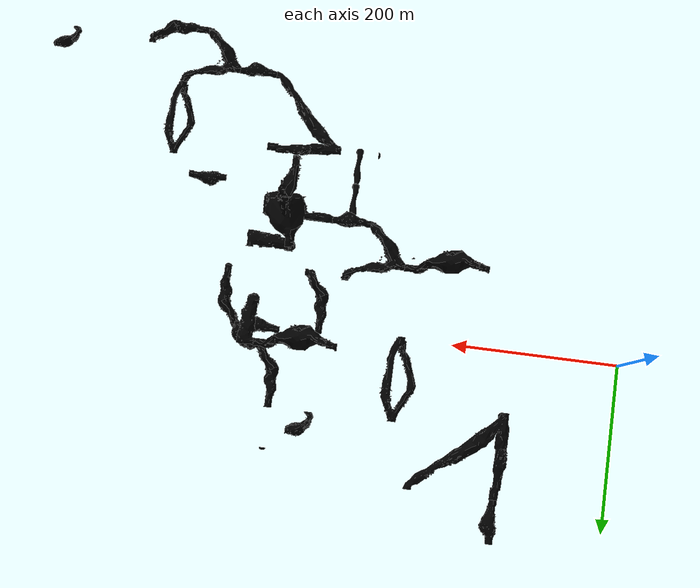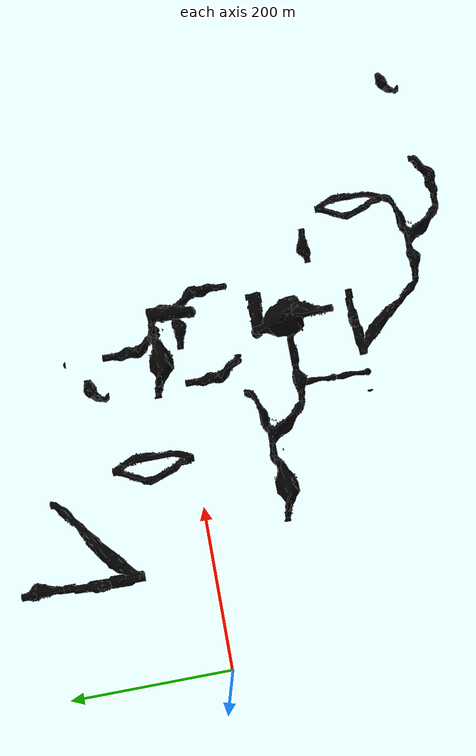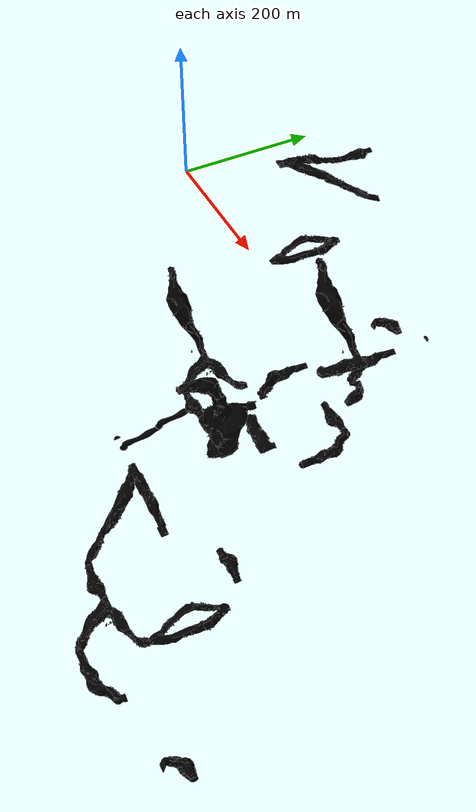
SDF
<sdf version="1.6">
 <world name="cave_circuit_03">
  <physics name="1ms" type="ode">
   <max_step_size>0.004</max_step_size>
   <real_time_factor>1.0</real_time_factor>
  </physics>
  <scene>
   <ambient>0.1 0.1 0.1 1.0</ambient>
   <background>0 0 0 1.0</background>
   <grid>false</grid>
   <origin_visual>false</origin_visual>
  </scene>
  <atmosphere type="adiabatic">
   <temperature>288</temperature>
   <temperature_gradient>0.2</temperature_gradient>
  </atmosphere>
  <model name="performer_detector_rockfall_1">
   <static>true</static>
   <pose>230.806000 131.221000 29.773300 0.0 0.0 0.0</pose>
   <plugin filename="libignition-gazebo-performer-detector-system.so" name="ignition::gazebo::systems::PerformerDetector">
    <topic>/subt_performer_detector</topic>
    <geometry><box><size>25 16 15</size></box></geometry>
   </plugin>
   <plugin name="ignition::gazebo::systems::TriggeredPublisher" filename="libignition-gazebo-triggered-publisher-system.so">
    <input type="ignition.msgs.Pose" topic="/subt_performer_detector">
     <match field="header.data">{
            key: "frame_id"
            value: "performer_detector_rockfall_1"
            }</match>
     <match field="header.data">{
            key: "state"
            value: "0"
            }</match>
    </input>
    <output type="ignition.msgs.Empty" topic="/model/dynamic_rocks_1/breadcrumbs/Rock/deploy"/>
   </plugin>
  </model>
  <model name="performer_detector_rockfall_2">
   <static>true</static>
   <pose>179.400000 -103.004000 -20.046300 0.0 0.0 0.0</pose>
   <plugin filename="libignition-gazebo-performer-detector-system.so" name="ignition::gazebo::systems::PerformerDetector">
    <topic>/subt_performer_detector</topic>
    <geometry><box><size>25 16 15</size></box></geometry>
   </plugin>
   <plugin name="ignition::gazebo::systems::TriggeredPublisher" filename="libignition-gazebo-triggered-publisher-system.so">
    <input type="ignition.msgs.Pose" topic="/subt_performer_detector">
     <match field="header.data">{
            key: "frame_id"
            value: "performer_detector_rockfall_2"
            }</match>
     <match field="header.data">{
            key: "state"
            value: "0"
            }</match>
    </input>
    <output type="ignition.msgs.Empty" topic="/model/dynamic_rocks_2/breadcrumbs/Rock/deploy"/>
   </plugin>
  </model>
  <model name="performer_detector_rockfall_3">
   <static>true</static>
   <pose>298.764000 -30.154900 23.041800 0 0 0</pose>
   <plugin filename="libignition-gazebo-performer-detector-system.so" name="ignition::gazebo::systems::PerformerDetector">
    <topic>/subt_performer_detector</topic>
    <geometry><box><size>16 25 15</size></box></geometry>
   </plugin>
   <plugin name="ignition::gazebo::systems::TriggeredPublisher" filename="libignition-gazebo-triggered-publisher-system.so">
    <input type="ignition.msgs.Pose" topic="/subt_performer_detector">
     <match field="header.data">{
            key: "frame_id"
            value: "performer_detector_rockfall_3"
            }</match>
     <match field="header.data">{
            key: "state"
            value: "1"
            }</match>
    </input>
    <output type="ignition.msgs.Empty" topic="/model/dynamic_rocks_3/breadcrumbs/Rock/deploy"/>
   </plugin>
  </model>
  <include>
   <static>true</static>
   <name>tile_1</name>
   <pose>412.5 -150.0 -50.0 0.0 0.0 -3.14159</pose>
   <uri>https://fuel.ignitionrobotics.org/1.0/OpenRobotics/models/Cave 3 Way Elevation 03 Type A</uri>
  </include>
  <include>
   <static>true</static>
   <name>tile_3</name>
   <pose>412.5 75.0 -50.0 0.0 0.0 0.0</pose>
   <uri>https://fuel.ignitionrobotics.org/1.0/OpenRobotics/models/Cave Corner 02 Lights Type A</uri>
  </include>
  <include>
   <static>true</static>
   <name>tile_5</name>
   <pose>137.5 200.0 50.0 0.0 0.0 0.0</pose>
   <uri>https://fuel.ignitionrobotics.org/1.0/OpenRobotics/models/Cave Straight Lights Type A</uri>
  </include>
  <include>
   <static>true</static>
   <name>tile_7</name>
   <pose>262.5 50.0 25.0 0.0 0.0 0.0</pose>
   <uri>https://fuel.ignitionrobotics.org/1.0/OpenRobotics/models/Cave Split Type A</uri>
  </include>
  <include>
   <static>true</static>
   <name>tile_8</name>
   <pose>462.5 25.0 -50.0 -1.95472e-06 0.0 -1.95505e-06</pose>
   <uri>https://fuel.ignitionrobotics.org/1.0/OpenRobotics/models/Cave Corner 03 Type A</uri>
  </include>
  <include>
   <static>true</static>
   <name>tile_9</name>
   <pose>212.5 -100.0 -100.0 0.0 0.0 0.0</pose>
   <uri>https://fuel.ignitionrobotics.org/1.0/OpenRobotics/models/Cave Elevation 02 Type A</uri>
  </include>
  <include>
   <static>true</static>
   <name>tile_10</name>
   <pose>337.5 -150.0 -100.0 0.0 0.0 1.5708</pose>
   <uri>https://fuel.ignitionrobotics.org/1.0/OpenRobotics/models/Cave Vertical Shaft Straight Top Type A</uri>
  </include>
  <include>
   <static>true</static>
   <name>tile_11</name>
   <pose>287.5 -100.0 -100.0 0.0 0.0 -1.5708</pose>
   <uri>https://fuel.ignitionrobotics.org/1.0/OpenRobotics/models/Cave 3 Way 01 Type A</uri>
  </include>
  <include>
   <static>true</static>
   <name>tile_14</name>
   <pose>412.5 -200.0 25.0 0.0 0.0 3.14159</pose>
   <uri>https://fuel.ignitionrobotics.org/1.0/OpenRobotics/models/Cave Cap Type A</uri>
  </include>
  <include>
   <static>true</static>
   <name>tile_18</name>
   <pose>412.5 150.0 -50.0 0.0 0.0 -1.74846e-07</pose>
   <uri>https://fuel.ignitionrobotics.org/1.0/OpenRobotics/models/Cave Cap Type A</uri>
  </include>
  <include>
   <static>true</static>
   <name>tile_19</name>
   <pose>437.5 0.0 0.0 0.0 0.0 -1.5708</pose>
   <uri>https://fuel.ignitionrobotics.org/1.0/OpenRobotics/models/Cave 2 Way 01 Type A</uri>
  </include>
  <include>
   <static>true</static>
   <name>tile_20</name>
   <pose>387.5 25.0 0.0 0.0 0.0 0.0</pose>
   <uri>https://fuel.ignitionrobotics.org/1.0/OpenRobotics/models/Cave Elevation 02 Type A</uri>
  </include>
  <include>
   <static>true</static>
   <name>tile_22</name>
   <pose>137.5 125.0 75.0 0.0 0.0 3.14159</pose>
   <uri>https://fuel.ignitionrobotics.org/1.0/OpenRobotics/models/Cave 3 Way Elevation 01 Type A</uri>
  </include>
  <include>
   <static>true</static>
   <name>tile_29</name>
   <pose>437.5 -100.0 -75.0 0.0 0.0 -3.14159</pose>
   <uri>https://fuel.ignitionrobotics.org/1.0/OpenRobotics/models/Cave 2 Way 01 Type A</uri>
  </include>
  <include>
   <static>true</static>
   <name>tile_31</name>
   <pose>437.5 0.0 -100.0 0.0 0.0 -1.5708</pose>
   <uri>https://fuel.ignitionrobotics.org/1.0/OpenRobotics/models/Cave Straight Type A</uri>
  </include>
  <include>
   <static>true</static>
   <name>tile_32</name>
   <pose>487.5 -50.0 -100.0 0.0 0.0 3.14159</pose>
   <uri>https://fuel.ignitionrobotics.org/1.0/OpenRobotics/models/Cave Corner 02 Type A</uri>
  </include>
  <include>
   <static>true</static>
   <name>tile_33</name>
   <pose>487.5 -75.0 -100.0 0.0 0.0 3.14159</pose>
   <uri>https://fuel.ignitionrobotics.org/1.0/OpenRobotics/models/Cave Cap Type A</uri>
  </include>
  <include>
   <static>true</static>
   <name>tile_35</name>
   <pose>337.5 -200.0 -125.0 0.0 0.0 -1.74846e-07</pose>
   <uri>https://fuel.ignitionrobotics.org/1.0/OpenRobotics/models/Cave Vertical Shaft Cantilevered Type A</uri>
  </include>
  <include>
   <static>true</static>
   <name>tile_36</name>
   <pose>337.5 -250.0 -140.0 0.0 0.0 -1.74846e-07</pose>
   <uri>https://fuel.ignitionrobotics.org/1.0/OpenRobotics/models/Cave Vertical Shaft Cantilevered Type A</uri>
  </include>
  <include>
   <static>true</static>
   <name>tile_37</name>
   <pose>412.5 -250.0 -140.0 0.0 0.0 1.5708</pose>
   <uri>https://fuel.ignitionrobotics.org/1.0/OpenRobotics/models/Cave 3 Way Elevation 01 Type A</uri>
  </include>
  <include>
   <static>true</static>
   <name>tile_38</name>
   <pose>312.5 -250.0 -140.0 0.0 0.0 1.5708</pose>
   <uri>https://fuel.ignitionrobotics.org/1.0/OpenRobotics/models/Cave Cap Type A</uri>
  </include>
  <include>
   <static>true</static>
   <name>tile_39</name>
   <pose>362.5 125.0 -50.0 0.0 0.0 1.57079</pose>
   <uri>https://fuel.ignitionrobotics.org/1.0/OpenRobotics/models/Cave Corner 03 Type A</uri>
  </include>
  <include>
   <static>true</static>
   <name>tile_40</name>
   <pose>487.5 -350.0 -165.0 0.0 0.0 -1.5708</pose>
   <uri>https://fuel.ignitionrobotics.org/1.0/OpenRobotics/models/Cave Straight Type A</uri>
  </include>
  <include>
   <static>true</static>
   <name>tile_42</name>
   <pose>537.5 -350.0 -165.0 0.0 0.0 -1.5708</pose>
   <uri>https://fuel.ignitionrobotics.org/1.0/OpenRobotics/models/Cave 3 Way 01 Type A</uri>
  </include>
  <include>
   <static>true</static>
   <name>tile_43</name>
   <pose>537.5 -200.0 -165.0 0.0 0.0 1.5708</pose>
   <uri>https://fuel.ignitionrobotics.org/1.0/OpenRobotics/models/Cave Straight Lights Type A</uri>
  </include>
  <include>
   <static>true</static>
   <name>tile_45</name>
   <pose>587.5 -275.0 -165.0 0.0 0.0 0.0</pose>
   <uri>https://fuel.ignitionrobotics.org/1.0/OpenRobotics/models/Cave Split Type A</uri>
  </include>
  <include>
   <static>true</static>
   <name>tile_46</name>
   <pose>587.5 -400.0 -165.0 0.0 0.0 1.5708</pose>
   <uri>https://fuel.ignitionrobotics.org/1.0/OpenRobotics/models/Cave Corner 02 Lights Type A</uri>
  </include>
  <include>
   <static>true</static>
   <name>tile_49</name>
   <pose>737.5 -350.0 -140.0 0.0 0.0 1.57079</pose>
   <uri>https://fuel.ignitionrobotics.org/1.0/OpenRobotics/models/Cave Corner 03 Type A</uri>
  </include>
  <include>
   <static>true</static>
   <name>tile_51</name>
   <pose>362.5 -25.0 -75.0 0.0 0.0 0.0</pose>
   <uri>https://fuel.ignitionrobotics.org/1.0/OpenRobotics/models/Cave Corner 02 Lights Type A</uri>
  </include>
  <include>
   <static>true</static>
   <name>tile_53</name>
   <pose>762.5 -350.0 -140.0 0.0 0.0 -1.5708</pose>
   <uri>https://fuel.ignitionrobotics.org/1.0/OpenRobotics/models/Cave Cap Type A</uri>
  </include>
  <plugin name="ignition::gazebo" filename="dummy">
   <level name="level0">
    <ref>tile_54</ref>
    <pose>37.5 -25 -40.2615 0 0 0</pose>
    <geometry><box><size>337.5 1110 529.571</size></box></geometry>
    <buffer>12.5</buffer>
   </level>
   <level name="level1">
    <ref>phone_4</ref>
    <pose>41.8534 -25 -40.2615 0 0 0</pose>
    <geometry><box><size>337.5 1110 529.571</size></box></geometry>
    <buffer>12.5</buffer>
   </level>
   <level name="level2">
    <ref>tile_12</ref>
    <pose>112.5 -25 -40.2615 0 0 0</pose>
    <geometry><box><size>337.5 1110 529.571</size></box></geometry>
    <buffer>12.5</buffer>
   </level>
   <level name="level3">
    <ref>backpack_2</ref>
    <pose>118.776 -25 -40.2615 0 0 0</pose>
    <geometry><box><size>337.5 1110 529.571</size></box></geometry>
    <buffer>12.5</buffer>
   </level>
   <level name="level4">
    <ref>rope_1</ref>
    <pose>131.189 -25 -40.2615 0 0 0</pose>
    <geometry><box><size>337.5 1110 529.571</size></box></geometry>
    <buffer>12.5</buffer>
   </level>
   <level name="level5">
    <ref>tile_5</ref>
    <ref>tile_22</ref>
    <ref>tile_27</ref>
    <pose>137.5 -25 -40.2615 0 0 0</pose>
    <geometry><box><size>337.5 1110 529.571</size></box></geometry>
    <buffer>12.5</buffer>
   </level>
   <level name="level6">
    <ref>phone_3</ref>
    <pose>141.826 -25 -40.2615 0 0 0</pose>
    <geometry><box><size>337.5 1110 529.571</size></box></geometry>
    <buffer>12.5</buffer>
   </level>
   <level name="level7">
    <ref>tile_25</ref>
    <pose>162.5 -25 -40.2615 0 0 0</pose>
    <geometry><box><size>337.5 1110 529.571</size></box></geometry>
    <buffer>12.5</buffer>
   </level>
   <level name="level8">
    <ref>backpack_4</ref>
    <pose>175.701 -25 -40.2615 0 0 0</pose>
    <geometry><box><size>337.5 1110 529.571</size></box></geometry>
    <buffer>12.5</buffer>
   </level>
   <level name="level9">
    <ref>helmet_2</ref>
    <pose>179.927 -25 -40.2615 0 0 0</pose>
    <geometry><box><size>337.5 1110 529.571</size></box></geometry>
    <buffer>12.5</buffer>
   </level>
   <level name="level10">
    <ref>rescue_randy_3</ref>
    <pose>182.833 -25 -40.2615 0 0 0</pose>
    <geometry><box><size>337.5 1110 529.571</size></box></geometry>
    <buffer>12.5</buffer>
   </level>
   <level name="level11">
    <ref>tile_16</ref>
    <ref>tile_26</ref>
    <pose>187.5 -25 -40.2615 0 0 0</pose>
    <geometry><box><size>337.5 1110 529.571</size></box></geometry>
    <buffer>12.5</buffer>
   </level>
   <level name="level12">
    <ref>tile_4</ref>
    <ref>tile_9</ref>
    <ref>tile_23</ref>
    <pose>212.5 -25 -40.2615 0 0 0</pose>
    <geometry><box><size>337.5 1110 529.571</size></box></geometry>
    <buffer>12.5</buffer>
   </level>
   <level name="level13">
    <ref>helmet_3</ref>
    <pose>228.514 -25 -40.2615 0 0 0</pose>
    <geometry><box><size>337.5 1110 529.571</size></box></geometry>
    <buffer>12.5</buffer>
   </level>
   <level name="level14">
    <ref>tile_13</ref>
    <pose>237.5 -25 -40.2615 0 0 0</pose>
    <geometry><box><size>337.5 1110 529.571</size></box></geometry>
    <buffer>12.5</buffer>
   </level>
   <level name="level15">
    <ref>tile_7</ref>
    <pose>262.5 -25 -40.2615 0 0 0</pose>
    <geometry><box><size>337.5 1110 529.571</size></box></geometry>
    <buffer>12.5</buffer>
   </level>
   <level name="level16">
    <ref>phone_1</ref>
    <pose>271.171 -25 -40.2615 0 0 0</pose>
    <geometry><box><size>337.5 1110 529.571</size></box></geometry>
    <buffer>12.5</buffer>
   </level>
   <level name="level17">
    <ref>tile_11</ref>
    <ref>tile_21</ref>
    <pose>287.5 -25 -40.2615 0 0 0</pose>
    <geometry><box><size>337.5 1110 529.571</size></box></geometry>
    <buffer>12.5</buffer>
   </level>
   <level name="level18">
    <ref>tile_38</ref>
    <pose>312.5 -25 -40.2615 0 0 0</pose>
    <geometry><box><size>337.5 1110 529.571</size></box></geometry>
    <buffer>12.5</buffer>
   </level>
   <level name="level19">
    <ref>rope_3</ref>
    <pose>318.279 -25 -40.2615 0 0 0</pose>
    <geometry><box><size>337.5 1110 529.571</size></box></geometry>
    <buffer>12.5</buffer>
   </level>
   <level name="level20">
    <ref>rescue_randy_4</ref>
    <pose>322.115 -25 -40.2615 0 0 0</pose>
    <geometry><box><size>337.5 1110 529.571</size></box></geometry>
    <buffer>12.5</buffer>
   </level>
   <level name="level21">
    <ref>tile_10</ref>
    <ref>tile_15</ref>
    <ref>tile_17</ref>
    <ref>tile_34</ref>
    <ref>tile_35</ref>
    <ref>tile_36</ref>
    <pose>337.5 -25 -40.2615 0 0 0</pose>
    <geometry><box><size>337.5 1110 529.571</size></box></geometry>
    <buffer>12.5</buffer>
   </level>
   <level name="level22">
    <ref>helmet_1</ref>
    <pose>351.976 -25 -40.2615 0 0 0</pose>
    <geometry><box><size>337.5 1110 529.571</size></box></geometry>
    <buffer>12.5</buffer>
   </level>
   <level name="level23">
    <ref>tile_39</ref>
    <ref>tile_51</ref>
    <ref>tile_52</ref>
    <pose>362.5 -25 -40.2615 0 0 0</pose>
    <geometry><box><size>337.5 1110 529.571</size></box></geometry>
    <buffer>12.5</buffer>
   </level>
   <level name="level24">
    <ref>helmet_4</ref>
    <pose>374.914 -25 -40.2615 0 0 0</pose>
    <geometry><box><size>337.5 1110 529.571</size></box></geometry>
    <buffer>12.5</buffer>
   </level>
   <level name="level25">
    <ref>rescue_randy_1</ref>
    <pose>378.857 -25 -40.2615 0 0 0</pose>
    <geometry><box><size>337.5 1110 529.571</size></box></geometry>
    <buffer>12.5</buffer>
   </level>
   <level name="level26">
    <ref>tile_20</ref>
    <ref>tile_24</ref>
    <pose>387.5 -25 -40.2615 0 0 0</pose>
    <geometry><box><size>337.5 1110 529.571</size></box></geometry>
    <buffer>12.5</buffer>
   </level>
   <level name="level27">
    <ref>rope_2</ref>
    <pose>409.013 -25 -40.2615 0 0 0</pose>
    <geometry><box><size>337.5 1110 529.571</size></box></geometry>
    <buffer>12.5</buffer>
   </level>
   <level name="level28">
    <ref>tile_1</ref>
    <ref>tile_2</ref>
    <ref>tile_3</ref>
    <ref>tile_6</ref>
    <ref>tile_14</ref>
    <ref>tile_18</ref>
    <ref>tile_37</ref>
    <ref>tile_50</ref>
    <pose>412.5 -25 -40.2615 0 0 0</pose>
    <geometry><box><size>337.5 1110 529.571</size></box></geometry>
    <buffer>12.5</buffer>
   </level>
   <level name="level29">
    <ref>rescue_randy_2</ref>
    <pose>422.862 -25 -40.2615 0 0 0</pose>
    <geometry><box><size>337.5 1110 529.571</size></box></geometry>
    <buffer>12.5</buffer>
   </level>
   <level name="level30">
    <ref>backpack_3</ref>
    <pose>423.582 -25 -40.2615 0 0 0</pose>
    <geometry><box><size>337.5 1110 529.571</size></box></geometry>
    <buffer>12.5</buffer>
   </level>
   <level name="level31">
    <ref>tile_19</ref>
    <ref>tile_29</ref>
    <ref>tile_31</ref>
    <pose>437.5 -25 -40.2615 0 0 0</pose>
    <geometry><box><size>337.5 1110 529.571</size></box></geometry>
    <buffer>12.5</buffer>
   </level>
   <level name="level32">
    <ref>tile_8</ref>
    <ref>tile_28</ref>
    <ref>tile_30</ref>
    <pose>462.5 -25 -40.2615 0 0 0</pose>
    <geometry><box><size>337.5 1110 529.571</size></box></geometry>
    <buffer>12.5</buffer>
   </level>
   <level name="level33">
    <ref>rope_4</ref>
    <pose>464.341 -25 -40.2615 0 0 0</pose>
    <geometry><box><size>337.5 1110 529.571</size></box></geometry>
    <buffer>12.5</buffer>
   </level>
   <level name="level34">
    <ref>tile_32</ref>
    <ref>tile_33</ref>
    <ref>tile_40</ref>
    <ref>tile_41</ref>
    <pose>487.5 -25 -40.2615 0 0 0</pose>
    <geometry><box><size>337.5 1110 529.571</size></box></geometry>
    <buffer>12.5</buffer>
   </level>
   <level name="level35">
    <ref>phone_2</ref>
    <pose>490.819 -25 -40.2615 0 0 0</pose>
    <geometry><box><size>337.5 1110 529.571</size></box></geometry>
    <buffer>12.5</buffer>
   </level>
   <level name="level36">
    <ref>tile_42</ref>
    <ref>tile_43</ref>
    <pose>537.5 -25 -40.2615 0 0 0</pose>
    <geometry><box><size>337.5 1110 529.571</size></box></geometry>
    <buffer>12.5</buffer>
   </level>
   <level name="level37">
    <ref>tile_44</ref>
    <ref>tile_45</ref>
    <ref>tile_46</ref>
    <pose>587.5 -25 -40.2615 0 0 0</pose>
    <geometry><box><size>337.5 1110 529.571</size></box></geometry>
    <buffer>12.5</buffer>
   </level>
   <level name="level38">
    <ref>tile_47</ref>
    <pose>687.5 -25 -40.2615 0 0 0</pose>
    <geometry><box><size>337.5 1110 529.571</size></box></geometry>
    <buffer>12.5</buffer>
   </level>
   <level name="level39">
    <ref>tile_48</ref>
    <pose>712.5 -25 -40.2615 0 0 0</pose>
    <geometry><box><size>337.5 1110 529.571</size></box></geometry>
    <buffer>12.5</buffer>
   </level>
   <level name="level40">
    <ref>tile_49</ref>
    <pose>737.5 -25 -40.2615 0 0 0</pose>
    <geometry><box><size>337.5 1110 529.571</size></box></geometry>
    <buffer>12.5</buffer>
   </level>
   <level name="level41">
    <ref>backpack_1</ref>
    <pose>759.133 -25 -40.2615 0 0 0</pose>
    <geometry><box><size>337.5 1110 529.571</size></box></geometry>
    <buffer>12.5</buffer>
   </level>
   <level name="level42">
    <ref>tile_53</ref>
    <pose>762.5 -25 -40.2615 0 0 0</pose>
    <geometry><box><size>337.5 1110 529.571</size></box></geometry>
    <buffer>12.5</buffer>
   </level>
   <level name="level43">
    <ref>tile_46</ref>
    <ref>tile_48</ref>
    <pose>400 -400 -40.2615 0 0 0</pose>
    <geometry><box><size>1085 337.5 529.571</size></box></geometry>
    <buffer>12.5</buffer>
   </level>
   <level name="level44">
    <ref>phone_2</ref>
    <pose>400 -357.455 -40.2615 0 0 0</pose>
    <geometry><box><size>1085 337.5 529.571</size></box></geometry>
    <buffer>12.5</buffer>
   </level>
   <level name="level45">
    <ref>tile_40</ref>
    <ref>tile_42</ref>
    <ref>tile_47</ref>
    <ref>tile_49</ref>
    <ref>tile_53</ref>
    <pose>400 -350 -40.2615 0 0 0</pose>
    <geometry><box><size>1085 337.5 529.571</size></box></geometry>
    <buffer>12.5</buffer>
   </level>
   <level name="level46">
    <ref>backpack_1</ref>
    <pose>400 -349.325 -40.2615 0 0 0</pose>
    <geometry><box><size>1085 337.5 529.571</size></box></geometry>
    <buffer>12.5</buffer>
   </level>
   <level name="level47">
    <ref>tile_45</ref>
    <pose>400 -275 -40.2615 0 0 0</pose>
    <geometry><box><size>1085 337.5 529.571</size></box></geometry>
    <buffer>12.5</buffer>
   </level>
   <level name="level48">
    <ref>tile_34</ref>
    <ref>tile_36</ref>
    <ref>tile_37</ref>
    <ref>tile_38</ref>
    <pose>400 -250 -40.2615 0 0 0</pose>
    <geometry><box><size>1085 337.5 529.571</size></box></geometry>
    <buffer>12.5</buffer>
   </level>
   <level name="level49">
    <ref>rescue_randy_4</ref>
    <pose>400 -246.141 -40.2615 0 0 0</pose>
    <geometry><box><size>1085 337.5 529.571</size></box></geometry>
    <buffer>12.5</buffer>
   </level>
   <level name="level50">
    <ref>rope_4</ref>
    <pose>400 -243.799 -40.2615 0 0 0</pose>
    <geometry><box><size>1085 337.5 529.571</size></box></geometry>
    <buffer>12.5</buffer>
   </level>
   <level name="level51">
    <ref>tile_41</ref>
    <pose>400 -225 -40.2615 0 0 0</pose>
    <geometry><box><size>1085 337.5 529.571</size></box></geometry>
    <buffer>12.5</buffer>
   </level>
   <level name="level52">
    <ref>tile_14</ref>
    <ref>tile_35</ref>
    <ref>tile_43</ref>
    <ref>tile_44</ref>
    <pose>400 -200 -40.2615 0 0 0</pose>
    <geometry><box><size>1085 337.5 529.571</size></box></geometry>
    <buffer>12.5</buffer>
   </level>
   <level name="level53">
    <ref>tile_1</ref>
    <ref>tile_10</ref>
    <pose>400 -150 -40.2615 0 0 0</pose>
    <geometry><box><size>1085 337.5 529.571</size></box></geometry>
    <buffer>12.5</buffer>
   </level>
   <level name="level54">
    <ref>backpack_3</ref>
    <pose>400 -118.786 -40.2615 0 0 0</pose>
    <geometry><box><size>1085 337.5 529.571</size></box></geometry>
    <buffer>12.5</buffer>
   </level>
   <level name="level55">
    <ref>backpack_4</ref>
    <pose>400 -103.294 -40.2615 0 0 0</pose>
    <geometry><box><size>1085 337.5 529.571</size></box></geometry>
    <buffer>12.5</buffer>
   </level>
   <level name="level56">
    <ref>tile_9</ref>
    <ref>tile_11</ref>
    <ref>tile_29</ref>
    <pose>400 -100 -40.2615 0 0 0</pose>
    <geometry><box><size>1085 337.5 529.571</size></box></geometry>
    <buffer>12.5</buffer>
   </level>
   <level name="level57">
    <ref>tile_33</ref>
    <ref>tile_50</ref>
    <pose>400 -75 -40.2615 0 0 0</pose>
    <geometry><box><size>1085 337.5 529.571</size></box></geometry>
    <buffer>12.5</buffer>
   </level>
   <level name="level58">
    <ref>rescue_randy_1</ref>
    <pose>400 -67.443 -40.2615 0 0 0</pose>
    <geometry><box><size>1085 337.5 529.571</size></box></geometry>
    <buffer>12.5</buffer>
   </level>
   <level name="level59">
    <ref>rope_1</ref>
    <pose>400 -64.6834 -40.2615 0 0 0</pose>
    <geometry><box><size>1085 337.5 529.571</size></box></geometry>
    <buffer>12.5</buffer>
   </level>
   <level name="level60">
    <ref>tile_15</ref>
    <ref>tile_28</ref>
    <ref>tile_32</ref>
    <pose>400 -50 -40.2615 0 0 0</pose>
    <geometry><box><size>1085 337.5 529.571</size></box></geometry>
    <buffer>12.5</buffer>
   </level>
   <level name="level61">
    <ref>helmet_1</ref>
    <pose>400 -43.5415 -40.2615 0 0 0</pose>
    <geometry><box><size>1085 337.5 529.571</size></box></geometry>
    <buffer>12.5</buffer>
   </level>
   <level name="level62">
    <ref>tile_17</ref>
    <ref>tile_24</ref>
    <ref>tile_51</ref>
    <pose>400 -25 -40.2615 0 0 0</pose>
    <geometry><box><size>1085 337.5 529.571</size></box></geometry>
    <buffer>12.5</buffer>
   </level>
   <level name="level63">
    <ref>helmet_4</ref>
    <pose>400 -22.6671 -40.2615 0 0 0</pose>
    <geometry><box><size>1085 337.5 529.571</size></box></geometry>
    <buffer>12.5</buffer>
   </level>
   <level name="level64">
    <ref>tile_6</ref>
    <ref>tile_12</ref>
    <ref>tile_19</ref>
    <ref>tile_31</ref>
    <ref>tile_54</ref>
    <pose>400 0 -40.2615 0 0 0</pose>
    <geometry><box><size>1085 337.5 529.571</size></box></geometry>
    <buffer>12.5</buffer>
   </level>
   <level name="level65">
    <ref>backpack_2</ref>
    <pose>400 0.52931 -40.2615 0 0 0</pose>
    <geometry><box><size>1085 337.5 529.571</size></box></geometry>
    <buffer>12.5</buffer>
   </level>
   <level name="level66">
    <ref>phone_4</ref>
    <pose>400 6.27248 -40.2615 0 0 0</pose>
    <geometry><box><size>1085 337.5 529.571</size></box></geometry>
    <buffer>12.5</buffer>
   </level>
   <level name="level67">
    <ref>rope_2</ref>
    <pose>400 16.1974 -40.2615 0 0 0</pose>
    <geometry><box><size>1085 337.5 529.571</size></box></geometry>
    <buffer>12.5</buffer>
   </level>
   <level name="level68">
    <ref>phone_3</ref>
    <pose>400 19.6901 -40.2615 0 0 0</pose>
    <geometry><box><size>1085 337.5 529.571</size></box></geometry>
    <buffer>12.5</buffer>
   </level>
   <level name="level69">
    <ref>rope_3</ref>
    <pose>400 23.8175 -40.2615 0 0 0</pose>
    <geometry><box><size>1085 337.5 529.571</size></box></geometry>
    <buffer>12.5</buffer>
   </level>
   <level name="level70">
    <ref>tile_8</ref>
    <ref>tile_16</ref>
    <ref>tile_20</ref>
    <ref>tile_21</ref>
    <pose>400 25 -40.2615 0 0 0</pose>
    <geometry><box><size>1085 337.5 529.571</size></box></geometry>
    <buffer>12.5</buffer>
   </level>
   <level name="level71">
    <ref>tile_4</ref>
    <ref>tile_7</ref>
    <ref>tile_52</ref>
    <pose>400 50 -40.2615 0 0 0</pose>
    <geometry><box><size>1085 337.5 529.571</size></box></geometry>
    <buffer>12.5</buffer>
   </level>
   <level name="level72">
    <ref>phone_1</ref>
    <pose>400 73.9939 -40.2615 0 0 0</pose>
    <geometry><box><size>1085 337.5 529.571</size></box></geometry>
    <buffer>12.5</buffer>
   </level>
   <level name="level73">
    <ref>tile_3</ref>
    <ref>tile_30</ref>
    <pose>400 75 -40.2615 0 0 0</pose>
    <geometry><box><size>1085 337.5 529.571</size></box></geometry>
    <buffer>12.5</buffer>
   </level>
   <level name="level74">
    <ref>helmet_3</ref>
    <pose>400 121.399 -40.2615 0 0 0</pose>
    <geometry><box><size>1085 337.5 529.571</size></box></geometry>
    <buffer>12.5</buffer>
   </level>
   <level name="level75">
    <ref>tile_2</ref>
    <ref>tile_13</ref>
    <ref>tile_22</ref>
    <ref>tile_39</ref>
    <pose>400 125 -40.2615 0 0 0</pose>
    <geometry><box><size>1085 337.5 529.571</size></box></geometry>
    <buffer>12.5</buffer>
   </level>
   <level name="level76">
    <ref>rescue_randy_3</ref>
    <pose>400 129.842 -40.2615 0 0 0</pose>
    <geometry><box><size>1085 337.5 529.571</size></box></geometry>
    <buffer>12.5</buffer>
   </level>
   <level name="level77">
    <ref>rescue_randy_2</ref>
    <pose>400 140.771 -40.2615 0 0 0</pose>
    <geometry><box><size>1085 337.5 529.571</size></box></geometry>
    <buffer>12.5</buffer>
   </level>
   <level name="level78">
    <ref>tile_18</ref>
    <pose>400 150 -40.2615 0 0 0</pose>
    <geometry><box><size>1085 337.5 529.571</size></box></geometry>
    <buffer>12.5</buffer>
   </level>
   <level name="level79">
    <ref>tile_5</ref>
    <ref>tile_23</ref>
    <pose>400 200 -40.2615 0 0 0</pose>
    <geometry><box><size>1085 337.5 529.571</size></box></geometry>
    <buffer>12.5</buffer>
   </level>
   <level name="level80">
    <ref>tile_26</ref>
    <ref>tile_27</ref>
    <pose>400 275 -40.2615 0 0 0</pose>
    <geometry><box><size>1085 337.5 529.571</size></box></geometry>
    <buffer>12.5</buffer>
   </level>
   <level name="level81">
    <ref>helmet_2</ref>
    <pose>400 337.194 -40.2615 0 0 0</pose>
    <geometry><box><size>1085 337.5 529.571</size></box></geometry>
    <buffer>12.5</buffer>
   </level>
   <level name="level82">
    <ref>tile_25</ref>
    <pose>400 350 -40.2615 0 0 0</pose>
    <geometry><box><size>1085 337.5 529.571</size></box></geometry>
    <buffer>12.5</buffer>
   </level>
  </plugin>
 </world>
</sdf>

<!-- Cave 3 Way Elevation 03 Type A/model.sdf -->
<sdf version="1.6">
  <model name="Cave 3 Way Elevation 03 Type A">
    <static>true</static>
    <link name="base_link">
      <collision name="collision">
        <pose>0 0 0 0 0 0</pose>
        <geometry>
          <mesh>
            <uri>model://Cave 3 Way Elevation 03 Type A/meshes/3wayelevation03.dae</uri>
            <scale>1.0 1.0 1.0</scale>
          </mesh>
        </geometry>
      </collision>
      <visual name="Gravel_visual">
        <geometry>
          <mesh>
            <uri>model://Cave 3 Way Elevation 03 Type A/meshes/3wayelevation03.dae</uri>
            <submesh>
              <name>Gravel</name>
              <center>false</center>
            </submesh>
          </mesh>
        </geometry>
        <material>
          <diffuse>0 0 0 1</diffuse>
          <specular>0 0 0 1</specular>
          <pbr>
            <metal>
              <albedo_map>model://Cave 3 Way Elevation 03 Type A/materials/textures/Gravel_Albedo.png</albedo_map>
              <normal_map>model://Cave 3 Way Elevation 03 Type A/materials/textures/Gravel_Normal.png</normal_map>
              <roughness_map>model://Cave 3 Way Elevation 03 Type A/materials/textures/Gravel_Roughness.png</roughness_map>
            </metal>
          </pbr>

          <script>
            <uri>model://Cave 3 Way Elevation 03 Type A/materials/scripts/</uri>
            <uri>model://Cave 3 Way Elevation 03 Type A/materials/textures/</uri>
            <name>CaveTile/Gravel_Diffuse</name>
          </script>
        </material>
      </visual>
      <visual name="StriatedRock_visual">
        <geometry>
          <mesh>
            <uri>model://Cave 3 Way Elevation 03 Type A/meshes/3wayelevation03.dae</uri>
            <submesh>
              <name>StriatedRock</name>
              <center>false</center>
            </submesh>
          </mesh>
        </geometry>
        <material>
          <diffuse>0 0 0 1</diffuse>
          <specular>0 0 0 1</specular>
          <pbr>
            <metal>
              <albedo_map>model://Cave 3 Way Elevation 03 Type A/materials/textures/StriatedRock_Albedo.png</albedo_map>
              <normal_map>model://Cave 3 Way Elevation 03 Type A/materials/textures/StriatedRock_Normal.png</normal_map>
              <roughness_map>model://Cave 3 Way Elevation 03 Type A/materials/textures/StriatedRock_Roughness.png</roughness_map>
            </metal>
          </pbr>

          <script>
            <uri>model://Cave 3 Way Elevation 03 Type A/materials/scripts/</uri>
            <uri>model://Cave 3 Way Elevation 03 Type A/materials/textures/</uri>
            <name>CaveTile/StriatedRock_Diffuse</name>
          </script>
        </material>
      </visual>
      <visual name="RockPile_visual">
        <geometry>
          <mesh>
            <uri>model://Cave 3 Way Elevation 03 Type A/meshes/3wayelevation03.dae</uri>
            <submesh>
              <name>RockPile</name>
              <center>false</center>
            </submesh>
          </mesh>
        </geometry>
        <material>
          <diffuse>0 0 0 1</diffuse>
          <specular>0 0 0 1</specular>
          <pbr>
            <metal>
              <albedo_map>model://Cave 3 Way Elevation 03 Type A/materials/textures/RockPile_Albedo.png</albedo_map>
              <normal_map>model://Cave 3 Way Elevation 03 Type A/materials/textures/RockPile_Normal.png</normal_map>
              <roughness_map>model://Cave 3 Way Elevation 03 Type A/materials/textures/RockPile_Roughness.png</roughness_map>
            </metal>
          </pbr>

          <script>
            <uri>model://Cave 3 Way Elevation 03 Type A/materials/scripts/</uri>
            <uri>model://Cave 3 Way Elevation 03 Type A/materials/textures/</uri>
            <name>CaveTile/RockPile_Diffuse</name>
          </script>
        </material>
      </visual>
      <visual name="CaveWall_visual">
        <geometry>
          <mesh>
            <uri>model://Cave 3 Way Elevation 03 Type A/meshes/3wayelevation03.dae</uri>
            <submesh>
              <name>CaveWall</name>
              <center>false</center>
            </submesh>
          </mesh>
        </geometry>
        <material>
          <diffuse>0 0 0 1</diffuse>
          <specular>0 0 0 1</specular>
          <pbr>
            <metal>
              <albedo_map>model://Cave 3 Way Elevation 03 Type A/materials/textures/CaveWall_Albedo.png</albedo_map>
              <normal_map>model://Cave 3 Way Elevation 03 Type A/materials/textures/CaveWall_Normal.png</normal_map>
              <roughness_map>model://Cave 3 Way Elevation 03 Type A/materials/textures/CaveWall_Roughness.png</roughness_map>
            </metal>
          </pbr>

          <script>
            <uri>model://Cave 3 Way Elevation 03 Type A/materials/scripts/</uri>
            <uri>model://Cave 3 Way Elevation 03 Type A/materials/textures/</uri>
            <name>CaveTile/CaveWall_Diffuse</name>
          </script>
        </material>
      </visual>
    </link>

    <plugin filename="libignition-gazebo-performer-detector-system.so" name="ignition::gazebo::systems::PerformerDetector">
      <topic>/subt_performer_detector</topic>
      <pose>-25 5 -30 0 0 0</pose>
      <header_data>
        <key>type</key>
        <value>vertical</value>
      </header_data>
      <geometry>
        <box>
          <size>25 25 10</size>
        </box>
      </geometry>
    </plugin>

    <plugin filename="libignition-gazebo-performer-detector-system.so" name="ignition::gazebo::systems::PerformerDetector">
      <topic>/subt_performer_detector</topic>
      <pose>-10 5 50 0 0 0</pose>
      <header_data>
        <key>type</key>
        <value>vertical</value>
      </header_data>
      <geometry>
        <box>
          <size>25 25 30</size>
        </box>
      </geometry>
    </plugin>

    <plugin filename="libignition-gazebo-performer-detector-system.so" name="ignition::gazebo::systems::PerformerDetector">
      <topic>/subt_performer_detector</topic>
      <pose>-10 0 0 0 0 0</pose>
      <header_data>
        <key>type</key>
        <value>decision, vertical</value>
      </header_data>
      <geometry>
        <box>
          <size>50 30 30</size>
        </box>
      </geometry>
    </plugin>
  </model>
</sdf>

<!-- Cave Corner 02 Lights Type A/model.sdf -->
<sdf version="1.6">
  <model name="Cave Corner 02 Lights Type A">
    <include>
      <name>cave_corner_02_type_a</name>
      <uri>model://Cave Corner 02 Type A</uri>
    </include>
    <static>true</static>
    <link name="lights">
      <light name="Omni009" type="spot">
        <pose>5.8147 -29.1165 5.08124 0 0 0</pose>
        <diffuse>0 0 0 1</diffuse>
        <specular>0 0 0 1</specular>
        <attenuation>
          <range>20</range>
          <linear>0.2</linear>
          <constant>1.0</constant>
          <quadratic>0.01</quadratic>
        </attenuation>
        <spot>
          <inner_angle>2.0</inner_angle>
          <outer_angle>3.1</outer_angle>
          <falloff>1.2</falloff>
        </spot>
        <cast_shadows>false</cast_shadows>
      </light>
      <light name="Omni010" type="spot">
        <pose>-1.05491 3.24461 2.89552 0 0 0</pose>
        <diffuse>0 0 0 1</diffuse>
        <specular>0 0 0 1</specular>
        <attenuation>
          <range>20</range>
          <linear>0.2</linear>
          <constant>1.0</constant>
          <quadratic>0.01</quadratic>
        </attenuation>
        <spot>
          <inner_angle>2.0</inner_angle>
          <outer_angle>3.1</outer_angle>
          <falloff>1.2</falloff>
        </spot>
        <cast_shadows>false</cast_shadows>
      </light>
    </link>
  </model>
</sdf>

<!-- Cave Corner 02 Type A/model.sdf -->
<sdf version="1.6">
  <model name="Cave Corner 02 Type A">
    <static>true</static>
    <link name="base_link">
      <collision name="collision">
        <pose>0 0 0 0 0 0</pose>
        <geometry>
          <mesh>
            <uri>model://Cave Corner 02 Type A/meshes/corner02.dae</uri>
            <scale>1.0 1.0 1.0</scale>
          </mesh>
        </geometry>
      </collision>
      <visual name="Gravel_visual">
        <geometry>
          <mesh>
            <uri>model://Cave Corner 02 Type A/meshes/corner02.dae</uri>
            <submesh>
              <name>Gravel</name>
              <center>false</center>
            </submesh>
          </mesh>
        </geometry>
        <material>
          <diffuse>0 0 0 1</diffuse>
          <specular>0 0 0 1</specular>
          <pbr>
            <metal>
              <albedo_map>model://Cave Corner 02 Type A/materials/textures/Gravel_Albedo.png</albedo_map>
              <normal_map>model://Cave Corner 02 Type A/materials/textures/Gravel_Normal.png</normal_map>
              <roughness_map>model://Cave Corner 02 Type A/materials/textures/Gravel_Roughness.png</roughness_map>
            </metal>
          </pbr>

          <script>
            <uri>model://Cave Corner 02 Type A/materials/scripts/</uri>
            <uri>model://Cave Corner 02 Type A/materials/textures/</uri>
            <name>CaveTile/Gravel_Diffuse</name>
          </script>
        </material>
      </visual>
      <visual name="RockPile_visual">
        <geometry>
          <mesh>
            <uri>model://Cave Corner 02 Type A/meshes/corner02.dae</uri>
            <submesh>
              <name>RockPile</name>
              <center>false</center>
            </submesh>
          </mesh>
        </geometry>
        <material>
          <diffuse>0 0 0 1</diffuse>
          <specular>0 0 0 1</specular>
          <pbr>
            <metal>
              <albedo_map>model://Cave Corner 02 Type A/materials/textures/RockPile_Albedo.png</albedo_map>
              <normal_map>model://Cave Corner 02 Type A/materials/textures/RockPile_Normal.png</normal_map>
              <roughness_map>model://Cave Corner 02 Type A/materials/textures/RockPile_Roughness.png</roughness_map>
            </metal>
          </pbr>

          <script>
            <uri>model://Cave Corner 02 Type A/materials/scripts/</uri>
            <uri>model://Cave Corner 02 Type A/materials/textures/</uri>
            <name>CaveTile/RockPile_Diffuse</name>
          </script>
        </material>
      </visual>
      <visual name="StriatedRock_visual">
        <geometry>
          <mesh>
            <uri>model://Cave Corner 02 Type A/meshes/corner02.dae</uri>
            <submesh>
              <name>StriatedRock</name>
              <center>false</center>
            </submesh>
          </mesh>
        </geometry>
        <material>
          <diffuse>0 0 0 1</diffuse>
          <specular>0 0 0 1</specular>
          <pbr>
            <metal>
              <albedo_map>model://Cave Corner 02 Type A/materials/textures/StriatedRock_Albedo.png</albedo_map>
              <normal_map>model://Cave Corner 02 Type A/materials/textures/StriatedRock_Normal.png</normal_map>
              <roughness_map>model://Cave Corner 02 Type A/materials/textures/StriatedRock_Roughness.png</roughness_map>
            </metal>
          </pbr>

          <script>
            <uri>model://Cave Corner 02 Type A/materials/scripts/</uri>
            <uri>model://Cave Corner 02 Type A/materials/textures/</uri>
            <name>CaveTile/StriatedRock_Diffuse</name>
          </script>
        </material>
      </visual>
      <visual name="CaveWall_visual">
        <geometry>
          <mesh>
            <uri>model://Cave Corner 02 Type A/meshes/corner02.dae</uri>
            <submesh>
              <name>CaveWall</name>
              <center>false</center>
            </submesh>
          </mesh>
        </geometry>
        <material>
          <diffuse>0 0 0 1</diffuse>
          <specular>0 0 0 1</specular>
          <pbr>
            <metal>
              <albedo_map>model://Cave Corner 02 Type A/materials/textures/CaveWall_Albedo.png</albedo_map>
              <normal_map>model://Cave Corner 02 Type A/materials/textures/CaveWall_Normal.png</normal_map>
              <roughness_map>model://Cave Corner 02 Type A/materials/textures/CaveWall_Roughness.png</roughness_map>
            </metal>
          </pbr>

          <script>
            <uri>model://Cave Corner 02 Type A/materials/scripts/</uri>
            <uri>model://Cave Corner 02 Type A/materials/textures/</uri>
            <name>CaveTile/CaveWall_Diffuse</name>
          </script>
        </material>
      </visual>
    </link>
  </model>
</sdf>

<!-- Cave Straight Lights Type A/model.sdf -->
<sdf version="1.6">
  <model name="Cave Straight Lights Type A">
    <include>
      <name>cave_straight_type_a</name>
      <uri>model://Cave Straight Type A</uri>
    </include>
    <static>true</static>
    <link name="lights">
      <light name="Omni011" type="spot">
        <pose>3.41296 1.14569 5.11374 0 0 0</pose>
        <diffuse>0 0 0 1</diffuse>
        <specular>0 0 0 1</specular>
        <attenuation>
          <range>20</range>
          <linear>0.2</linear>
          <constant>1.0</constant>
          <quadratic>0.01</quadratic>
        </attenuation>
        <spot>
          <inner_angle>2.0</inner_angle>
          <outer_angle>3.1</outer_angle>
          <falloff>1.2</falloff>
        </spot>
        <cast_shadows>false</cast_shadows>
      </light>
    </link>
  </model>
</sdf>

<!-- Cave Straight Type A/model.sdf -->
<sdf version="1.6">
  <model name="Cave Straight Type A">
    <static>true</static>
    <link name="base_link">
      <collision name="collision">
        <pose>0 0 0 0 0 0</pose>
        <geometry>
          <mesh>
            <uri>model://Cave Straight Type A/meshes/straight.dae</uri>
            <scale>1.0 1.0 1.0</scale>
          </mesh>
        </geometry>
      </collision>
      <visual name="Gravel_visual">
        <geometry>
          <mesh>
            <uri>model://Cave Straight Type A/meshes/straight.dae</uri>
            <submesh>
              <name>Gravel</name>
              <center>false</center>
            </submesh>
          </mesh>
        </geometry>
        <material>
          <diffuse>0 0 0 1</diffuse>
          <specular>0 0 0 1</specular>
          <pbr>
            <metal>
              <albedo_map>model://Cave Straight Type A/materials/textures/Gravel_Albedo.png</albedo_map>
              <normal_map>model://Cave Straight Type A/materials/textures/Gravel_Normal.png</normal_map>
              <roughness_map>model://Cave Straight Type A/materials/textures/Gravel_Roughness.png</roughness_map>
            </metal>
          </pbr>

          <script>
            <uri>model://Cave Straight Type A/materials/scripts/</uri>
            <uri>model://Cave Straight Type A/materials/textures/</uri>
            <name>CaveTile/Gravel_Diffuse</name>
          </script>
        </material>
      </visual>
      <visual name="RockPile_visual">
        <geometry>
          <mesh>
            <uri>model://Cave Straight Type A/meshes/straight.dae</uri>
            <submesh>
              <name>RockPile</name>
              <center>false</center>
            </submesh>
          </mesh>
        </geometry>
        <material>
          <diffuse>0 0 0 1</diffuse>
          <specular>0 0 0 1</specular>
          <pbr>
            <metal>
              <albedo_map>model://Cave Straight Type A/materials/textures/RockPile_Albedo.png</albedo_map>
              <normal_map>model://Cave Straight Type A/materials/textures/RockPile_Normal.png</normal_map>
              <roughness_map>model://Cave Straight Type A/materials/textures/RockPile_Roughness.png</roughness_map>
            </metal>
          </pbr>

          <script>
            <uri>model://Cave Straight Type A/materials/scripts/</uri>
            <uri>model://Cave Straight Type A/materials/textures/</uri>
            <name>CaveTile/RockPile_Diffuse</name>
          </script>
        </material>
      </visual>
      <visual name="StriatedRock_visual">
        <geometry>
          <mesh>
            <uri>model://Cave Straight Type A/meshes/straight.dae</uri>
            <submesh>
              <name>StriatedRock</name>
              <center>false</center>
            </submesh>
          </mesh>
        </geometry>
        <material>
          <diffuse>0 0 0 1</diffuse>
          <specular>0 0 0 1</specular>
          <pbr>
            <metal>
              <albedo_map>model://Cave Straight Type A/materials/textures/StriatedRock_Albedo.png</albedo_map>
              <normal_map>model://Cave Straight Type A/materials/textures/StriatedRock_Normal.png</normal_map>
              <roughness_map>model://Cave Straight Type A/materials/textures/StriatedRock_Roughness.png</roughness_map>
            </metal>
          </pbr>

          <script>
            <uri>model://Cave Straight Type A/materials/scripts/</uri>
            <uri>model://Cave Straight Type A/materials/textures/</uri>
            <name>CaveTile/StriatedRock_Diffuse</name>
          </script>
        </material>
      </visual>
      <visual name="CaveWall_visual">
        <geometry>
          <mesh>
            <uri>model://Cave Straight Type A/meshes/straight.dae</uri>
            <submesh>
              <name>CaveWall</name>
              <center>false</center>
            </submesh>
          </mesh>
        </geometry>
        <material>
          <diffuse>0 0 0 1</diffuse>
          <specular>0 0 0 1</specular>
          <pbr>
            <metal>
              <albedo_map>model://Cave Straight Type A/materials/textures/CaveWall_Albedo.png</albedo_map>
              <normal_map>model://Cave Straight Type A/materials/textures/CaveWall_Normal.png</normal_map>
              <roughness_map>model://Cave Straight Type A/materials/textures/CaveWall_Roughness.png</roughness_map>
            </metal>
          </pbr>

          <script>
            <uri>model://Cave Straight Type A/materials/scripts/</uri>
            <uri>model://Cave Straight Type A/materials/textures/</uri>
            <name>CaveTile/CaveWall_Diffuse</name>
          </script>
        </material>
      </visual>
    </link>
  </model>
</sdf>

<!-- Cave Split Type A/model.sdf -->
<sdf version="1.6">
  <model name="Cave Split Type A">
    <static>true</static>
    <link name="base_link">
      <collision name="collision">
        <pose>0 0 0 0 0 0</pose>
        <geometry>
          <mesh>
            <uri>model://Cave Split Type A/meshes/split.dae</uri>
            <scale>1.0 1.0 1.0</scale>
          </mesh>
        </geometry>
      </collision>
      <visual name="Gravel_visual">
        <geometry>
          <mesh>
            <uri>model://Cave Split Type A/meshes/split.dae</uri>
            <submesh>
              <name>Gravel</name>
              <center>false</center>
            </submesh>
          </mesh>
        </geometry>
        <material>
          <diffuse>0 0 0 1</diffuse>
          <specular>0 0 0 1</specular>
          <pbr>
            <metal>
              <albedo_map>model://Cave Split Type A/materials/textures/Gravel_Albedo.png</albedo_map>
              <normal_map>model://Cave Split Type A/materials/textures/Gravel_Normal.png</normal_map>
              <roughness_map>model://Cave Split Type A/materials/textures/Gravel_Roughness.png</roughness_map>
            </metal>
          </pbr>

          <script>
            <uri>model://Cave Split Type A/materials/scripts/</uri>
            <uri>model://Cave Split Type A/materials/textures/</uri>
            <name>CaveTile/Gravel_Diffuse</name>
          </script>
        </material>
      </visual>
      <visual name="RockPile_visual">
        <geometry>
          <mesh>
            <uri>model://Cave Split Type A/meshes/split.dae</uri>
            <submesh>
              <name>RockPile</name>
              <center>false</center>
            </submesh>
          </mesh>
        </geometry>
        <material>
          <diffuse>0 0 0 1</diffuse>
          <specular>0 0 0 1</specular>
          <pbr>
            <metal>
              <albedo_map>model://Cave Split Type A/materials/textures/RockPile_Albedo.png</albedo_map>
              <normal_map>model://Cave Split Type A/materials/textures/RockPile_Normal.png</normal_map>
              <roughness_map>model://Cave Split Type A/materials/textures/RockPile_Roughness.png</roughness_map>
            </metal>
          </pbr>

          <script>
            <uri>model://Cave Split Type A/materials/scripts/</uri>
            <uri>model://Cave Split Type A/materials/textures/</uri>
            <name>CaveTile/RockPile_Diffuse</name>
          </script>
        </material>
      </visual>
      <visual name="StriatedRock_visual">
        <geometry>
          <mesh>
            <uri>model://Cave Split Type A/meshes/split.dae</uri>
            <submesh>
              <name>StriatedRock</name>
              <center>false</center>
            </submesh>
          </mesh>
        </geometry>
        <material>
          <diffuse>0 0 0 1</diffuse>
          <specular>0 0 0 1</specular>
          <pbr>
            <metal>
              <albedo_map>model://Cave Split Type A/materials/textures/StriatedRock_Albedo.png</albedo_map>
              <normal_map>model://Cave Split Type A/materials/textures/StriatedRock_Normal.png</normal_map>
              <roughness_map>model://Cave Split Type A/materials/textures/StriatedRock_Roughness.png</roughness_map>
            </metal>
          </pbr>

          <script>
            <uri>model://Cave Split Type A/materials/scripts/</uri>
            <uri>model://Cave Split Type A/materials/textures/</uri>
            <name>CaveTile/StriatedRock_Diffuse</name>
          </script>
        </material>
      </visual>
      <visual name="CaveWall_visual">
        <geometry>
          <mesh>
            <uri>model://Cave Split Type A/meshes/split.dae</uri>
            <submesh>
              <name>CaveWall</name>
              <center>false</center>
            </submesh>
          </mesh>
        </geometry>
        <material>
          <diffuse>0 0 0 1</diffuse>
          <specular>0 0 0 1</specular>
          <pbr>
            <metal>
              <albedo_map>model://Cave Split Type A/materials/textures/CaveWall_Albedo.png</albedo_map>
              <normal_map>model://Cave Split Type A/materials/textures/CaveWall_Normal.png</normal_map>
              <roughness_map>model://Cave Split Type A/materials/textures/CaveWall_Roughness.png</roughness_map>
            </metal>
          </pbr>

          <script>
            <uri>model://Cave Split Type A/materials/scripts/</uri>
            <uri>model://Cave Split Type A/materials/textures/</uri>
            <name>CaveTile/CaveWall_Diffuse</name>
          </script>
        </material>
      </visual>
    </link>

    <plugin filename="libignition-gazebo-performer-detector-system.so" name="ignition::gazebo::systems::PerformerDetector">
      <topic>/subt_performer_detector</topic>
      <pose>0 -45 5 0 0 0</pose>
      <geometry>
        <box>
          <size>15 15 10</size>
        </box>
      </geometry>
      <header_data>
        <key>type</key>
        <value>decision</value>
      </header_data>
    </plugin>

    <plugin filename="libignition-gazebo-performer-detector-system.so" name="ignition::gazebo::systems::PerformerDetector">
      <topic>/subt_performer_detector</topic>
      <pose>0 45 5 0 0 0</pose>
      <geometry>
        <box>
          <size>15 15 10</size>
        </box>
      </geometry>
      <header_data>
        <key>type</key>
        <value>decision</value>
      </header_data>
    </plugin>
  </model>
</sdf>

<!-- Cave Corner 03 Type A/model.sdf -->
<sdf version="1.6">
  <model name="Cave Corner 03 Type A">
    <static>true</static>
    <link name="base_link">
      <collision name="collision">
        <pose>0 0 0 0 0 0</pose>
        <geometry>
          <mesh>
            <uri>model://Cave Corner 03 Type A/meshes/corner03.dae</uri>
            <scale>1.0 1.0 1.0</scale>
          </mesh>
        </geometry>
      </collision>
      <visual name="CaveWall_visual">
        <geometry>
          <mesh>
            <uri>model://Cave Corner 03 Type A/meshes/corner03.dae</uri>
            <submesh>
              <name>CaveWall</name>
              <center>false</center>
            </submesh>
          </mesh>
        </geometry>
        <material>
          <diffuse>0 0 0 1</diffuse>
          <specular>0 0 0 1</specular>
          <pbr>
            <metal>
              <albedo_map>model://Cave Corner 03 Type A/materials/textures/CaveWall_Albedo.png</albedo_map>
              <normal_map>model://Cave Corner 03 Type A/materials/textures/CaveWall_Normal.png</normal_map>
              <roughness_map>model://Cave Corner 03 Type A/materials/textures/CaveWall_Roughness.png</roughness_map>
            </metal>
          </pbr>

          <script>
            <uri>model://Cave Corner 03 Type A/materials/scripts/</uri>
            <uri>model://Cave Corner 03 Type A/materials/textures/</uri>
            <name>CaveTile/CaveWall_Diffuse</name>
          </script>
        </material>
      </visual>
      <visual name="Gravel_visual">
        <geometry>
          <mesh>
            <uri>model://Cave Corner 03 Type A/meshes/corner03.dae</uri>
            <submesh>
              <name>Gravel</name>
              <center>false</center>
            </submesh>
          </mesh>
        </geometry>
        <material>
          <diffuse>0 0 0 1</diffuse>
          <specular>0 0 0 1</specular>
          <pbr>
            <metal>
              <albedo_map>model://Cave Corner 03 Type A/materials/textures/Gravel_Albedo.png</albedo_map>
              <normal_map>model://Cave Corner 03 Type A/materials/textures/Gravel_Normal.png</normal_map>
              <roughness_map>model://Cave Corner 03 Type A/materials/textures/Gravel_Roughness.png</roughness_map>
            </metal>
          </pbr>

          <script>
            <uri>model://Cave Corner 03 Type A/materials/scripts/</uri>
            <uri>model://Cave Corner 03 Type A/materials/textures/</uri>
            <name>CaveTile/Gravel_Diffuse</name>
          </script>
        </material>
      </visual>
      <visual name="RockPile_visual">
        <geometry>
          <mesh>
            <uri>model://Cave Corner 03 Type A/meshes/corner03.dae</uri>
            <submesh>
              <name>RockPile</name>
              <center>false</center>
            </submesh>
          </mesh>
        </geometry>
        <material>
          <diffuse>0 0 0 1</diffuse>
          <specular>0 0 0 1</specular>
          <pbr>
            <metal>
              <albedo_map>model://Cave Corner 03 Type A/materials/textures/RockPile_Albedo.png</albedo_map>
              <normal_map>model://Cave Corner 03 Type A/materials/textures/RockPile_Normal.png</normal_map>
              <roughness_map>model://Cave Corner 03 Type A/materials/textures/RockPile_Roughness.png</roughness_map>
            </metal>
          </pbr>

          <script>
            <uri>model://Cave Corner 03 Type A/materials/scripts/</uri>
            <uri>model://Cave Corner 03 Type A/materials/textures/</uri>
            <name>CaveTile/RockPile_Diffuse</name>
          </script>
        </material>
      </visual>
      <visual name="StriatedRock_visual">
        <geometry>
          <mesh>
            <uri>model://Cave Corner 03 Type A/meshes/corner03.dae</uri>
            <submesh>
              <name>StriatedRock</name>
              <center>false</center>
            </submesh>
          </mesh>
        </geometry>
        <material>
          <diffuse>0 0 0 1</diffuse>
          <specular>0 0 0 1</specular>
          <pbr>
            <metal>
              <albedo_map>model://Cave Corner 03 Type A/materials/textures/StriatedRock_Albedo.png</albedo_map>
              <normal_map>model://Cave Corner 03 Type A/materials/textures/StriatedRock_Normal.png</normal_map>
              <roughness_map>model://Cave Corner 03 Type A/materials/textures/StriatedRock_Roughness.png</roughness_map>
            </metal>
          </pbr>

          <script>
            <uri>model://Cave Corner 03 Type A/materials/scripts/</uri>
            <uri>model://Cave Corner 03 Type A/materials/textures/</uri>
            <name>CaveTile/StriatedRock_Diffuse</name>
          </script>
        </material>
      </visual>
    </link>
  </model>
</sdf>

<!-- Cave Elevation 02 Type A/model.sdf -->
<sdf version="1.6">
  <model name="Cave Elevation 02 Type A">
    <static>true</static>
    <link name="base_link">
      <collision name="collision">
        <pose>0 0 0 0 0 0</pose>
        <geometry>
          <mesh>
            <uri>model://Cave Elevation 02 Type A/meshes/elevation02.dae</uri>
            <scale>1.0 1.0 1.0</scale>
          </mesh>
        </geometry>
      </collision>
      <visual name="Gravel_visual">
        <geometry>
          <mesh>
            <uri>model://Cave Elevation 02 Type A/meshes/elevation02.dae</uri>
            <submesh>
              <name>Gravel</name>
              <center>false</center>
            </submesh>
          </mesh>
        </geometry>
        <material>
          <diffuse>0 0 0 1</diffuse>
          <specular>0 0 0 1</specular>
          <pbr>
            <metal>
              <albedo_map>model://Cave Elevation 02 Type A/materials/textures/Gravel_Albedo.png</albedo_map>
              <normal_map>model://Cave Elevation 02 Type A/materials/textures/Gravel_Normal.png</normal_map>
              <roughness_map>model://Cave Elevation 02 Type A/materials/textures/Gravel_Roughness.png</roughness_map>
            </metal>
          </pbr>

          <script>
            <uri>model://Cave Elevation 02 Type A/materials/scripts/</uri>
            <uri>model://Cave Elevation 02 Type A/materials/textures/</uri>
            <name>CaveTile/Gravel_Diffuse</name>
          </script>
        </material>
      </visual>
      <visual name="RockPile_visual">
        <geometry>
          <mesh>
            <uri>model://Cave Elevation 02 Type A/meshes/elevation02.dae</uri>
            <submesh>
              <name>RockPile</name>
              <center>false</center>
            </submesh>
          </mesh>
        </geometry>
        <material>
          <diffuse>0 0 0 1</diffuse>
          <specular>0 0 0 1</specular>
          <pbr>
            <metal>
              <albedo_map>model://Cave Elevation 02 Type A/materials/textures/RockPile_Albedo.png</albedo_map>
              <normal_map>model://Cave Elevation 02 Type A/materials/textures/RockPile_Normal.png</normal_map>
              <roughness_map>model://Cave Elevation 02 Type A/materials/textures/RockPile_Roughness.png</roughness_map>
            </metal>
          </pbr>

          <script>
            <uri>model://Cave Elevation 02 Type A/materials/scripts/</uri>
            <uri>model://Cave Elevation 02 Type A/materials/textures/</uri>
            <name>CaveTile/RockPile_Diffuse</name>
          </script>
        </material>
      </visual>
      <visual name="StriatedRock_visual">
        <geometry>
          <mesh>
            <uri>model://Cave Elevation 02 Type A/meshes/elevation02.dae</uri>
            <submesh>
              <name>StriatedRock</name>
              <center>false</center>
            </submesh>
          </mesh>
        </geometry>
        <material>
          <diffuse>0 0 0 1</diffuse>
          <specular>0 0 0 1</specular>
          <pbr>
            <metal>
              <albedo_map>model://Cave Elevation 02 Type A/materials/textures/StriatedRock_Albedo.png</albedo_map>
              <normal_map>model://Cave Elevation 02 Type A/materials/textures/StriatedRock_Normal.png</normal_map>
              <roughness_map>model://Cave Elevation 02 Type A/materials/textures/StriatedRock_Roughness.png</roughness_map>
            </metal>
          </pbr>

          <script>
            <uri>model://Cave Elevation 02 Type A/materials/scripts/</uri>
            <uri>model://Cave Elevation 02 Type A/materials/textures/</uri>
            <name>CaveTile/StriatedRock_Diffuse</name>
          </script>
        </material>
      </visual>
      <visual name="CaveWall_visual">
        <geometry>
          <mesh>
            <uri>model://Cave Elevation 02 Type A/meshes/elevation02.dae</uri>
            <submesh>
              <name>CaveWall</name>
              <center>false</center>
            </submesh>
          </mesh>
        </geometry>
        <material>
          <diffuse>0 0 0 1</diffuse>
          <specular>0 0 0 1</specular>
          <pbr>
            <metal>
              <albedo_map>model://Cave Elevation 02 Type A/materials/textures/CaveWall_Albedo.png</albedo_map>
              <normal_map>model://Cave Elevation 02 Type A/materials/textures/CaveWall_Normal.png</normal_map>
              <roughness_map>model://Cave Elevation 02 Type A/materials/textures/CaveWall_Roughness.png</roughness_map>
            </metal>
          </pbr>

          <script>
            <uri>model://Cave Elevation 02 Type A/materials/scripts/</uri>
            <uri>model://Cave Elevation 02 Type A/materials/textures/</uri>
            <name>CaveTile/CaveWall_Diffuse</name>
          </script>
        </material>
      </visual>
    </link>

    <plugin filename="libignition-gazebo-performer-detector-system.so" name="ignition::gazebo::systems::PerformerDetector">
      <header_data>
        <key>type</key>
        <value>vertical</value>
      </header_data>
      <topic>/subt_performer_detector</topic>
      <pose>2.25 -7 42.5 0 0 0</pose>
      <geometry>
        <box>
          <size>58.5 31 81</size>
        </box>
      </geometry>
    </plugin>
  </model>
</sdf>

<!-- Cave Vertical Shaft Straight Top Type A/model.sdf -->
<sdf version="1.6">
  <model name="Cave Vertical Shaft Straight Top Type A">
    <static>true</static>
    <link name="base_link">
      <collision name="collision">
        <pose>0 0 0 0 0 0</pose>
        <geometry>
          <mesh>
            <uri>model://Cave Vertical Shaft Straight Top Type A/meshes/verticalshaftstraighttop.dae</uri>
            <scale>1.0 1.0 1.0</scale>
          </mesh>
        </geometry>
      </collision>
      <visual name="Gravel_visual">
        <geometry>
          <mesh>
            <uri>model://Cave Vertical Shaft Straight Top Type A/meshes/verticalshaftstraighttop.dae</uri>
            <submesh>
              <name>Gravel</name>
              <center>false</center>
            </submesh>
          </mesh>
        </geometry>
        <material>
          <diffuse>0 0 0 1</diffuse>
          <specular>0 0 0 1</specular>
          <pbr>
            <metal>
              <albedo_map>model://Cave Vertical Shaft Straight Top Type A/materials/textures/Gravel_Albedo.png</albedo_map>
              <normal_map>model://Cave Vertical Shaft Straight Top Type A/materials/textures/Gravel_Normal.png</normal_map>
              <roughness_map>model://Cave Vertical Shaft Straight Top Type A/materials/textures/Gravel_Roughness.png</roughness_map>
            </metal>
          </pbr>

          <script>
            <uri>model://Cave Vertical Shaft Straight Top Type A/materials/scripts/</uri>
            <uri>model://Cave Vertical Shaft Straight Top Type A/materials/textures/</uri>
            <name>CaveTile/Gravel_Diffuse</name>
          </script>
        </material>
      </visual>
      <visual name="StriatedRock_visual">
        <geometry>
          <mesh>
            <uri>model://Cave Vertical Shaft Straight Top Type A/meshes/verticalshaftstraighttop.dae</uri>
            <submesh>
              <name>StriatedRock</name>
              <center>false</center>
            </submesh>
          </mesh>
        </geometry>
        <material>
          <diffuse>0 0 0 1</diffuse>
          <specular>0 0 0 1</specular>
          <pbr>
            <metal>
              <albedo_map>model://Cave Vertical Shaft Straight Top Type A/materials/textures/StriatedRock_Albedo.png</albedo_map>
              <normal_map>model://Cave Vertical Shaft Straight Top Type A/materials/textures/StriatedRock_Normal.png</normal_map>
              <roughness_map>model://Cave Vertical Shaft Straight Top Type A/materials/textures/StriatedRock_Roughness.png</roughness_map>
            </metal>
          </pbr>

          <script>
            <uri>model://Cave Vertical Shaft Straight Top Type A/materials/scripts/</uri>
            <uri>model://Cave Vertical Shaft Straight Top Type A/materials/textures/</uri>
            <name>CaveTile/StriatedRock_Diffuse</name>
          </script>
        </material>
      </visual>
      <visual name="RockPile_visual">
        <geometry>
          <mesh>
            <uri>model://Cave Vertical Shaft Straight Top Type A/meshes/verticalshaftstraighttop.dae</uri>
            <submesh>
              <name>RockPile</name>
              <center>false</center>
            </submesh>
          </mesh>
        </geometry>
        <material>
          <diffuse>0 0 0 1</diffuse>
          <specular>0 0 0 1</specular>
          <pbr>
            <metal>
              <albedo_map>model://Cave Vertical Shaft Straight Top Type A/materials/textures/RockPile_Albedo.png</albedo_map>
              <normal_map>model://Cave Vertical Shaft Straight Top Type A/materials/textures/RockPile_Normal.png</normal_map>
              <roughness_map>model://Cave Vertical Shaft Straight Top Type A/materials/textures/RockPile_Roughness.png</roughness_map>
            </metal>
          </pbr>

          <script>
            <uri>model://Cave Vertical Shaft Straight Top Type A/materials/scripts/</uri>
            <uri>model://Cave Vertical Shaft Straight Top Type A/materials/textures/</uri>
            <name>CaveTile/RockPile_Diffuse</name>
          </script>
        </material>
      </visual>
      <visual name="CaveWall_visual">
        <geometry>
          <mesh>
            <uri>model://Cave Vertical Shaft Straight Top Type A/meshes/verticalshaftstraighttop.dae</uri>
            <submesh>
              <name>CaveWall</name>
              <center>false</center>
            </submesh>
          </mesh>
        </geometry>
        <material>
          <diffuse>0 0 0 1</diffuse>
          <specular>0 0 0 1</specular>
          <pbr>
            <metal>
              <albedo_map>model://Cave Vertical Shaft Straight Top Type A/materials/textures/CaveWall_Albedo.png</albedo_map>
              <normal_map>model://Cave Vertical Shaft Straight Top Type A/materials/textures/CaveWall_Normal.png</normal_map>
              <roughness_map>model://Cave Vertical Shaft Straight Top Type A/materials/textures/CaveWall_Roughness.png</roughness_map>
            </metal>
          </pbr>

          <script>
            <uri>model://Cave Vertical Shaft Straight Top Type A/materials/scripts/</uri>
           <uri>model://Cave Vertical Shaft Straight Top Type A/materials/textures/</uri>
            <name>CaveTile/CaveWall_Diffuse</name>
          </script>
        </material>
      </visual>
    </link>

    <plugin filename="libignition-gazebo-performer-detector-system.so" name="ignition::gazebo::systems::PerformerDetector">
      <topic>/subt_performer_detector</topic>
      <pose>-3 0 5 0 0 0</pose>
      <geometry>
        <box>
          <size>15 10 10</size>
        </box>
      </geometry>
      <header_data>
        <key>type</key>
        <value>vertical</value>
      </header_data>
    </plugin>
  </model>
</sdf>

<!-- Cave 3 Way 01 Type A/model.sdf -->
<sdf version="1.6">
  <model name="Cave 3 Way 01 Type A">
    <static>true</static>
    <link name="base_link">
      <collision name="collision">
        <pose>0 0 0 0 0 0</pose>
        <geometry>
          <mesh>
            <uri>model://Cave 3 Way 01 Type A/meshes/3way01.dae</uri>
            <scale>1.0 1.0 1.0</scale>
          </mesh>
        </geometry>
      </collision>
      <visual name="Gravel_visual">
        <geometry>
          <mesh>
            <uri>model://Cave 3 Way 01 Type A/meshes/3way01.dae</uri>
            <submesh>
              <name>Gravel</name>
              <center>false</center>
            </submesh>
          </mesh>
        </geometry>
        <material>
          <diffuse>0 0 0 1</diffuse>
          <specular>0 0 0 1</specular>
          <pbr>
            <metal>
              <albedo_map>model://Cave 3 Way 01 Type A/materials/textures/Gravel_Albedo.png</albedo_map>
              <normal_map>model://Cave 3 Way 01 Type A/materials/textures/Gravel_Normal.png</normal_map>
              <roughness_map>model://Cave 3 Way 01 Type A/materials/textures/Gravel_Roughness.png</roughness_map>
            </metal>
          </pbr>

          <script>
            <uri>model://Cave 3 Way 01 Type A/materials/scripts/</uri>
            <uri>model://Cave 3 Way 01 Type A/materials/textures/</uri>
            <name>CaveTile/Gravel_Diffuse</name>
          </script>
        </material>
      </visual>
      <visual name="StriatedRock_visual">
        <geometry>
          <mesh>
            <uri>model://Cave 3 Way 01 Type A/meshes/3way01.dae</uri>
            <submesh>
              <name>StriatedRock</name>
              <center>false</center>
            </submesh>
          </mesh>
        </geometry>
        <material>
          <diffuse>0 0 0 1</diffuse>
          <specular>0 0 0 1</specular>
          <pbr>
            <metal>
              <albedo_map>model://Cave 3 Way 01 Type A/materials/textures/StriatedRock_Albedo.png</albedo_map>
              <normal_map>model://Cave 3 Way 01 Type A/materials/textures/StriatedRock_Normal.png</normal_map>
              <roughness_map>model://Cave 3 Way 01 Type A/materials/textures/StriatedRock_Roughness.png</roughness_map>
            </metal>
          </pbr>

          <script>
            <uri>model://Cave 3 Way 01 Type A/materials/scripts/</uri>
            <uri>model://Cave 3 Way 01 Type A/materials/textures/</uri>
            <name>CaveTile/StriatedRock_Diffuse</name>
          </script>
        </material>
      </visual>
      <visual name="RockPile_visual">
        <geometry>
          <mesh>
            <uri>model://Cave 3 Way 01 Type A/meshes/3way01.dae</uri>
            <submesh>
              <name>RockPile</name>
              <center>false</center>
            </submesh>
          </mesh>
        </geometry>
        <material>
          <diffuse>0 0 0 1</diffuse>
          <specular>0 0 0 1</specular>
          <pbr>
            <metal>
              <albedo_map>model://Cave 3 Way 01 Type A/materials/textures/RockPile_Albedo.png</albedo_map>
              <normal_map>model://Cave 3 Way 01 Type A/materials/textures/RockPile_Normal.png</normal_map>
              <roughness_map>model://Cave 3 Way 01 Type A/materials/textures/RockPile_Roughness.png</roughness_map>
            </metal>
          </pbr>

          <script>
            <uri>model://Cave 3 Way 01 Type A/materials/scripts/</uri>
            <uri>model://Cave 3 Way 01 Type A/materials/textures/</uri>
            <name>CaveTile/RockPile_Diffuse</name>
          </script>
        </material>
      </visual>
      <visual name="CaveWall_visual">
        <geometry>
          <mesh>
            <uri>model://Cave 3 Way 01 Type A/meshes/3way01.dae</uri>
            <submesh>
              <name>CaveWall</name>
              <center>false</center>
            </submesh>
          </mesh>
        </geometry>
        <material>
          <diffuse>0 0 0 1</diffuse>
          <specular>0 0 0 1</specular>
          <pbr>
            <metal>
              <albedo_map>model://Cave 3 Way 01 Type A/materials/textures/CaveWall_Albedo.png</albedo_map>
              <normal_map>model://Cave 3 Way 01 Type A/materials/textures/CaveWall_Normal.png</normal_map>
              <roughness_map>model://Cave 3 Way 01 Type A/materials/textures/CaveWall_Roughness.png</roughness_map>
            </metal>
          </pbr>

          <script>
            <uri>model://Cave 3 Way 01 Type A/materials/scripts/</uri>
            <uri>model://Cave 3 Way 01 Type A/materials/textures/</uri>
            <name>CaveTile/CaveWall_Diffuse</name>
          </script>
        </material>
      </visual>
    </link>

    <plugin filename="libignition-gazebo-performer-detector-system.so" name="ignition::gazebo::systems::PerformerDetector">
      <topic>/subt_performer_detector</topic>
      <pose>5 -12 5 0 0 0</pose>
      <header_data>
        <key>type</key>
        <value>decision</value>
      </header_data>
      <geometry>
        <box>
          <size>20 20 15</size>
        </box>
      </geometry>
    </plugin>
  </model>
</sdf>

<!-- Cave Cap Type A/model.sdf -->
<sdf version="1.6">
  <model name="Cave Cap Type A">
    <static>true</static>
    <link name="base_link">
      <collision name="collision">
        <pose>0 0 0 0 0 0</pose>
        <geometry>
          <mesh>
            <uri>model://Cave Cap Type A/meshes/cap.dae</uri>
            <scale>1.0 1.0 1.0</scale>
          </mesh>
        </geometry>
      </collision>
      <visual name="Cave Cap Type A_visual">
        <geometry>
          <mesh>
            <uri>model://Cave Cap Type A/meshes/cap.dae</uri>
          </mesh>
        </geometry>
        <material>
          <diffuse>0 0 0 1</diffuse>
          <specular>0 0 0 1</specular>
          <pbr>
            <metal>
              <albedo_map>model://Cave Cap Type A/materials/textures/CaveWall_Albedo.png</albedo_map>
              <normal_map>model://Cave Cap Type A/materials/textures/CaveWall_Normal.png</normal_map>
              <roughness_map>model://Cave Cap Type A/materials/textures/CaveWall_Roughness.png</roughness_map>
            </metal>
          </pbr>

          <script>
            <uri>model://Cave Cap Type A/materials/scripts/</uri>
            <uri>model://Cave Cap Type A/materials/textures/</uri>
            <name>CaveTile/CaveWall_Diffuse</name>
          </script>
        </material>
      </visual>
    </link>
  </model>
</sdf>

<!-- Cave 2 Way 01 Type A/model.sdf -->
<sdf version="1.6">
  <model name="Cave 2 Way 01 Type A">
    <static>true</static>
    <link name="base_link">
      <collision name="collision">
        <pose>0 0 0 0 0 0</pose>
        <geometry>
          <mesh>
            <uri>model://Cave 2 Way 01 Type A/meshes/2way01.dae</uri>
            <scale>1.0 1.0 1.0</scale>
          </mesh>
        </geometry>
      </collision>
      <visual name="Gravel_visual">
        <geometry>
          <mesh>
            <uri>model://Cave 2 Way 01 Type A/meshes/2way01.dae</uri>
            <submesh>
              <name>Gravel</name>
              <center>false</center>
            </submesh>
          </mesh>
        </geometry>
        <material>
          <diffuse>0 0 0 1</diffuse>

          <pbr>
            <metal>
              <albedo_map>model://Cave 2 Way 01 Type A/materials/textures/Gravel_Albedo.png</albedo_map>
              <normal_map>model://Cave 2 Way 01 Type A/materials/textures/Gravel_Normal.png</normal_map>
              <roughness_map>model://Cave 2 Way 01 Type A/materials/textures/Gravel_Roughness.png</roughness_map>
            </metal>
          </pbr>

          <script>
            <uri>model://Cave 2 Way 01 Type A/materials/scripts/</uri>
            <uri>model://Cave 2 Way 01 Type A/materials/textures/</uri>
            <name>CaveTile/Gravel_Diffuse</name>
          </script>
        </material>
      </visual>
      <visual name="RockPile_visual">
        <geometry>
          <mesh>
            <uri>model://Cave 2 Way 01 Type A/meshes/2way01.dae</uri>
            <submesh>
              <name>RockPile</name>
              <center>false</center>
            </submesh>
          </mesh>
        </geometry>
        <material>
          <diffuse>0 0 0 1</diffuse>
          <specular>0 0 0 1</specular>
          <pbr>
            <metal>
              <albedo_map>model://Cave 2 Way 01 Type A/materials/textures/RockPile_Albedo.png</albedo_map>
              <normal_map>model://Cave 2 Way 01 Type A/materials/textures/RockPile_Normal.png</normal_map>
              <roughness_map>model://Cave 2 Way 01 Type A/materials/textures/RockPile_Roughness.png</roughness_map>
            </metal>
          </pbr>

          <script>
            <uri>model://Cave 2 Way 01 Type A/materials/scripts/</uri>
            <uri>model://Cave 2 Way 01 Type A/materials/textures/</uri>
            <name>CaveTile/RockPile_Diffuse</name>
          </script>
        </material>
      </visual>
      <visual name="StriatedRock_visual">
        <geometry>
          <mesh>
            <uri>model://Cave 2 Way 01 Type A/meshes/2way01.dae</uri>
            <submesh>
              <name>StriatedRock</name>
              <center>false</center>
            </submesh>
          </mesh>
        </geometry>
        <material>
          <diffuse>0 0 0 1</diffuse>
          <specular>0 0 0 1</specular>
          <pbr>
            <metal>
              <albedo_map>model://Cave 2 Way 01 Type A/materials/textures/StriatedRock_Albedo.png</albedo_map>
              <normal_map>model://Cave 2 Way 01 Type A/materials/textures/StriatedRock_Normal.png</normal_map>
              <roughness_map>model://Cave 2 Way 01 Type A/materials/textures/StriatedRock_Roughness.png</roughness_map>
            </metal>
          </pbr>

          <script>
            <uri>model://Cave 2 Way 01 Type A/materials/scripts/</uri>
            <uri>model://Cave 2 Way 01 Type A/materials/textures/</uri>
            <name>CaveTile/StriatedRock_Diffuse</name>
          </script>
        </material>
      </visual>
      <visual name="CaveWall_visual">
        <geometry>
          <mesh>
            <uri>model://Cave 2 Way 01 Type A/meshes/2way01.dae</uri>
            <submesh>
              <name>CaveWall</name>
              <center>false</center>
            </submesh>
          </mesh>
        </geometry>
        <material>
          <diffuse>0 0 0 1</diffuse>
          <specular>0 0 0 1</specular>
          <pbr>
            <metal>
              <albedo_map>model://Cave 2 Way 01 Type A/materials/textures/CaveWall_Albedo.png</albedo_map>
              <normal_map>model://Cave 2 Way 01 Type A/materials/textures/CaveWall_Normal.png</normal_map>
              <roughness_map>model://Cave 2 Way 01 Type A/materials/textures/CaveWall_Roughness.png</roughness_map>
            </metal>
          </pbr>

          <script>
            <uri>model://Cave 2 Way 01 Type A/materials/scripts/</uri>
            <uri>model://Cave 2 Way 01 Type A/materials/textures/</uri>
            <name>CaveTile/CaveWall_Diffuse</name>
          </script>
        </material>
      </visual>
    </link>
  </model>
</sdf>

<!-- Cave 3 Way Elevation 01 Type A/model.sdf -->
<sdf version="1.6">
  <model name="Cave 3 Way Elevation 01 Type A">
    <static>true</static>
    <link name="base_link">
      <collision name="collision">
        <pose>0 0 0 0 0 0</pose>
        <geometry>
          <mesh>
            <uri>model://Cave 3 Way Elevation 01 Type A/meshes/3wayelevation01.dae</uri>
            <scale>1.0 1.0 1.0</scale>
          </mesh>
        </geometry>
      </collision>
      <visual name="CaveWall_visual">
        <geometry>
          <mesh>
            <uri>model://Cave 3 Way Elevation 01 Type A/meshes/3wayelevation01.dae</uri>
            <submesh>
              <name>CaveWall</name>
              <center>false</center>
            </submesh>
          </mesh>
        </geometry>
        <material>
          <diffuse>0 0 0 1</diffuse>
          <specular>0 0 0 1</specular>
          <pbr>
            <metal>
              <albedo_map>model://Cave 3 Way Elevation 01 Type A/materials/textures/CaveWall_Albedo.png</albedo_map>
              <normal_map>model://Cave 3 Way Elevation 01 Type A/materials/textures/CaveWall_Normal.png</normal_map>
              <roughness_map>model://Cave 3 Way Elevation 01 Type A/materials/textures/CaveWall_Roughness.png</roughness_map>
            </metal>
          </pbr>

          <script>
            <uri>model://Cave 3 Way Elevation 01 Type A/materials/scripts/</uri>
            <uri>model://Cave 3 Way Elevation 01 Type A/materials/textures/</uri>
            <name>CaveTile/CaveWall_Diffuse</name>
          </script>
        </material>
      </visual>
      <visual name="Gravel_visual">
        <geometry>
          <mesh>
            <uri>model://Cave 3 Way Elevation 01 Type A/meshes/3wayelevation01.dae</uri>
            <submesh>
              <name>Gravel</name>
              <center>false</center>
            </submesh>
          </mesh>
        </geometry>
        <material>
          <diffuse>0 0 0 1</diffuse>
          <specular>0 0 0 1</specular>
          <pbr>
            <metal>
              <albedo_map>model://Cave 3 Way Elevation 01 Type A/materials/textures/Gravel_Albedo.png</albedo_map>
              <normal_map>model://Cave 3 Way Elevation 01 Type A/materials/textures/Gravel_Normal.png</normal_map>
              <roughness_map>model://Cave 3 Way Elevation 01 Type A/materials/textures/Gravel_Roughness.png</roughness_map>
            </metal>
          </pbr>

          <script>
            <uri>model://Cave 3 Way Elevation 01 Type A/materials/scripts/</uri>
            <uri>model://Cave 3 Way Elevation 01 Type A/materials/textures/</uri>
            <name>CaveTile/Gravel_Diffuse</name>
          </script>
        </material>
      </visual>
      <visual name="StriatedRock_visual">
        <geometry>
          <mesh>
            <uri>model://Cave 3 Way Elevation 01 Type A/meshes/3wayelevation01.dae</uri>
            <submesh>
              <name>StriatedRock</name>
              <center>false</center>
            </submesh>
          </mesh>
        </geometry>
        <material>
          <diffuse>0 0 0 1</diffuse>
          <specular>0 0 0 1</specular>
          <pbr>
            <metal>
              <albedo_map>model://Cave 3 Way Elevation 01 Type A/materials/textures/StriatedRock_Albedo.png</albedo_map>
              <normal_map>model://Cave 3 Way Elevation 01 Type A/materials/textures/StriatedRock_Normal.png</normal_map>
              <roughness_map>model://Cave 3 Way Elevation 01 Type A/materials/textures/StriatedRock_Roughness.png</roughness_map>
            </metal>
          </pbr>

          <script>
            <uri>model://Cave 3 Way Elevation 01 Type A/materials/scripts/</uri>
            <uri>model://Cave 3 Way Elevation 01 Type A/materials/textures/</uri>
            <name>CaveTile/StriatedRock_Diffuse</name>
          </script>
        </material>
      </visual>
      <visual name="RockPile_visual">
        <geometry>
          <mesh>
            <uri>model://Cave 3 Way Elevation 01 Type A/meshes/3wayelevation01.dae</uri>
            <submesh>
              <name>RockPile</name>
              <center>false</center>
            </submesh>
          </mesh>
        </geometry>
        <material>
          <diffuse>0 0 0 1</diffuse>
          <specular>0 0 0 1</specular>
          <pbr>
            <metal>
              <albedo_map>model://Cave 3 Way Elevation 01 Type A/materials/textures/RockPile_Albedo.png</albedo_map>
              <normal_map>model://Cave 3 Way Elevation 01 Type A/materials/textures/RockPile_Normal.png</normal_map>
              <roughness_map>model://Cave 3 Way Elevation 01 Type A/materials/textures/RockPile_Roughness.png</roughness_map>
            </metal>
          </pbr>

          <script>
            <uri>model://Cave 3 Way Elevation 01 Type A/materials/scripts/</uri>
            <uri>model://Cave 3 Way Elevation 01 Type A/materials/textures/</uri>
            <name>CaveTile/RockPile_Diffuse</name>
          </script>
        </material>
      </visual>
    </link>

    <plugin filename="libignition-gazebo-performer-detector-system.so" name="ignition::gazebo::systems::PerformerDetector">
      <topic>/subt_performer_detector</topic>
      <pose>-3.2 42.5 1.7 0 0 0</pose>
      <header_data>
        <key>type</key>
        <value>decision</value>
      </header_data>
      <geometry>
        <box>
          <size>15 15 7</size>
        </box>
      </geometry>
    </plugin>
    <plugin filename="libignition-gazebo-performer-detector-system.so" name="ignition::gazebo::systems::PerformerDetector">
      <topic>/subt_performer_detector</topic>
      <pose>-50 0 -6.5 0 0 0</pose>
      <header_data>
        <key>type</key>
        <value>elevation</value>
      </header_data>
      <geometry>
        <box>
          <size>40 40 20</size>
        </box>
      </geometry>
    </plugin>
  </model>
</sdf>

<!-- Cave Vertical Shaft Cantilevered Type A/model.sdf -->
<sdf version="1.6">
  <model name="Cave Vertical Shaft Cantilevered Type A">
    <static>true</static>
    <link name="base_link">
      <collision name="collision">
        <pose>0 0 0 0 0 0</pose>
        <geometry>
          <mesh>
            <uri>model://Cave Vertical Shaft Cantilevered Type A/meshes/verticalshaftcantilevered.dae</uri>
            <scale>1.0 1.0 1.0</scale>
          </mesh>
        </geometry>
      </collision>
      <visual name="Cave Vertical Shaft Cantilevered Type A_visual">
        <geometry>
          <mesh>
            <uri>model://Cave Vertical Shaft Cantilevered Type A/meshes/verticalshaftcantilevered.dae</uri>
          </mesh>
        </geometry>
        <material>
          <diffuse>0 0 0 1</diffuse>
          <specular>0 0 0 1</specular>
          <pbr>
            <metal>
              <albedo_map>model://Cave Vertical Shaft Cantilevered Type A/materials/textures/CaveWall_Albedo.png</albedo_map>
              <normal_map>model://Cave Vertical Shaft Cantilevered Type A/materials/textures/CaveWall_Normal.png</normal_map>
              <roughness_map>model://Cave Vertical Shaft Cantilevered Type A/materials/textures/CaveWall_Roughness.png</roughness_map>
            </metal>
          </pbr>

          <script>
            <uri>model://Cave Vertical Shaft Cantilevered Type A/materials/scripts/</uri>
            <uri>model://Cave Vertical Shaft Cantilevered Type A/materials/textures/</uri>
            <name>CaveTile/CaveWall_Diffuse</name>
          </script>
        </material>
      </visual>
    </link>
  </model>
</sdf>
